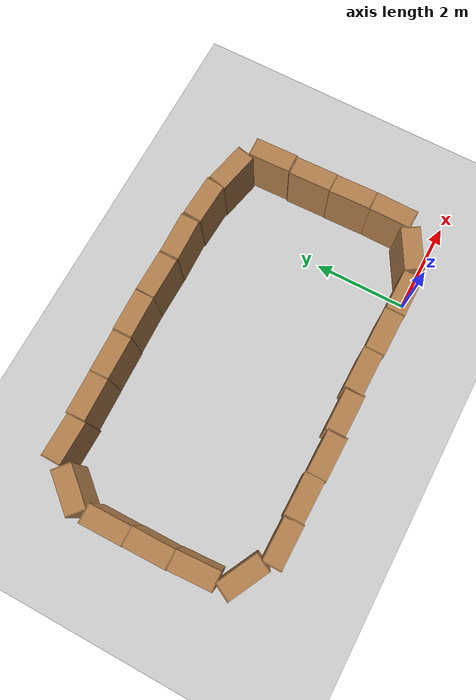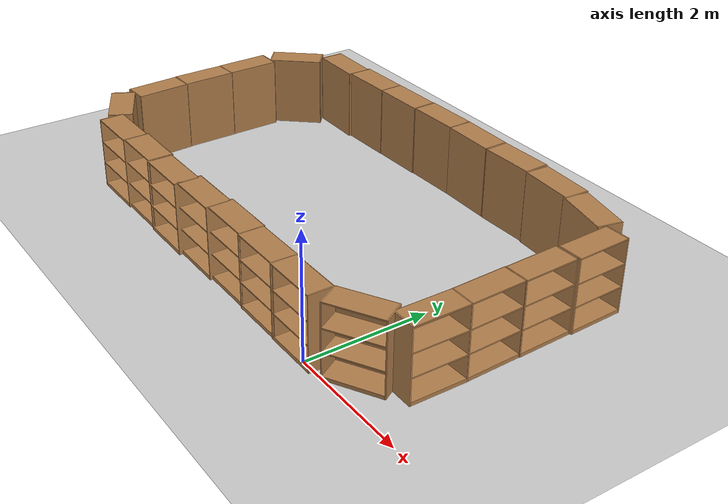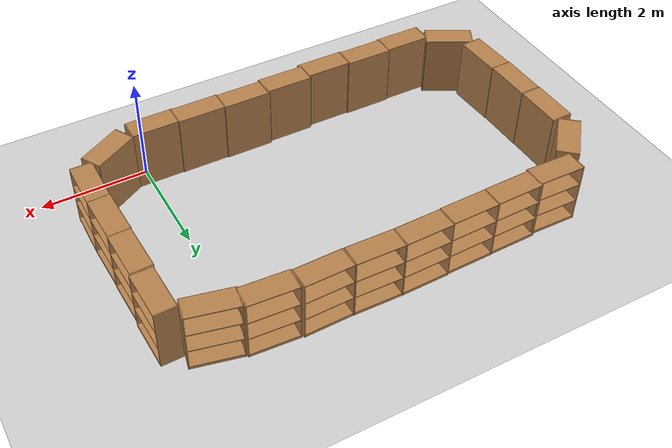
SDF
<sdf version="1.4">
 <world name="default">
  <light name="sun" type="directional">
   <pose>0 0 10 0 -0 0</pose>
   <diffuse>0.8 0.8 0.8 1</diffuse>
   <specular>0.2 0.2 0.2 1</specular>
   <attenuation>
    <range>1000</range>
    <constant>0.9</constant>
    <linear>0.01</linear>
    <quadratic>0.001</quadratic>
   </attenuation>
   <direction>-0.5 0.1 -0.9</direction>
  </light>
  <model name="ground_plane">
   <static>1</static>
   <link name="link">
    <collision name="collision">
     <geometry><plane><normal>0 0 1</normal><size>100 100</size></plane></geometry>
     <surface><friction><ode><mu>100</mu><mu2>50</mu2></ode></friction></surface>
    </collision>
    <visual name="visual">
     <cast_shadows>0</cast_shadows>
     <geometry><plane><normal>0 0 1</normal><size>100 100</size></plane></geometry>
     <material>
      <script><uri>file://media/materials/scripts/gazebo.material</uri><name>Gazebo/Grey</name></script>
     </material>
    </visual>
    <velocity_decay><linear>0</linear><angular>0</angular></velocity_decay>
   </link>
  </model>
  <physics type="ode">
   <max_step_size>0.01</max_step_size>
   <real_time_factor>1</real_time_factor>
   <real_time_update_rate>100</real_time_update_rate>
   <gravity>0 0 -9.8</gravity>
  </physics>
  <scene><ambient>0.4 0.4 0.4 1</ambient><background>0.7 0.7 0.7 1</background><shadows>1</shadows></scene>
  <model name="bookshelf">
   <static>1</static>
   <link name="link">
    <inertial><mass>1</mass></inertial>
    <collision name="back">
     <pose>0 0.005 0.6 0 -0 0</pose>
     <geometry><box><size>0.9 0.01 1.2</size></box></geometry>
    </collision>
    <visual name="visual1">
     <pose>0 0.005 0.6 0 -0 0</pose>
     <geometry><box><size>0.9 0.01 1.2</size></box></geometry>
     <material>
      <script><uri>file://media/materials/scripts/gazebo.material</uri><name>Gazebo/Wood</name></script>
     </material>
    </visual>
    <collision name="left_side">
     <pose>0.45 -0.195 0.6 0 -0 0</pose>
     <geometry><box><size>0.02 0.4 1.2</size></box></geometry>
    </collision>
    <visual name="visual2">
     <pose>0.45 -0.195 0.6 0 -0 0</pose>
     <geometry><box><size>0.02 0.4 1.2</size></box></geometry>
     <material>
      <script><uri>file://media/materials/scripts/gazebo.material</uri><name>Gazebo/Wood</name></script>
     </material>
    </visual>
    <collision name="right_side">
     <pose>-0.45 -0.195 0.6 0 -0 0</pose>
     <geometry><box><size>0.02 0.4 1.2</size></box></geometry>
    </collision>
    <visual name="visual3">
     <pose>-0.45 -0.195 0.6 0 -0 0</pose>
     <geometry><box><size>0.02 0.4 1.2</size></box></geometry>
     <material>
      <script><uri>file://media/materials/scripts/gazebo.material</uri><name>Gazebo/Wood</name></script>
     </material>
    </visual>
    <collision name="bottom">
     <pose>0 -0.195 0.03 0 -0 0</pose>
     <geometry><box><size>0.88 0.4 0.06</size></box></geometry>
    </collision>
    <visual name="visual4">
     <pose>0 -0.195 0.03 0 -0 0</pose>
     <geometry><box><size>0.88 0.4 0.06</size></box></geometry>
     <material>
      <script><uri>file://media/materials/scripts/gazebo.material</uri><name>Gazebo/Wood</name></script>
     </material>
    </visual>
    <collision name="top">
     <pose>0 -0.195 1.19 0 -0 0</pose>
     <geometry><box><size>0.88 0.4 0.02</size></box></geometry>
    </collision>
    <visual name="visual5">
     <pose>0 -0.195 1.19 0 -0 0</pose>
     <geometry><box><size>0.88 0.4 0.02</size></box></geometry>
     <material>
      <script><uri>file://media/materials/scripts/gazebo.material</uri><name>Gazebo/Wood</name></script>
     </material>
    </visual>
    <collision name="low_shelf">
     <pose>0 -0.195 0.43 0 -0 0</pose>
     <geometry><box><size>0.88 0.4 0.02</size></box></geometry>
    </collision>
    <visual name="visual6">
     <pose>0 -0.195 0.43 0 -0 0</pose>
     <geometry><box><size>0.88 0.4 0.02</size></box></geometry>
     <material>
      <script><uri>file://media/materials/scripts/gazebo.material</uri><name>Gazebo/Wood</name></script>
     </material>
    </visual>
    <collision name="high_shelf">
     <pose>0 -0.195 0.8 0 -0 0</pose>
     <geometry><box><size>0.88 0.4 0.02</size></box></geometry>
    </collision>
    <visual name="visual7">
     <pose>0 -0.195 0.8 0 -0 0</pose>
     <geometry><box><size>0.88 0.4 0.02</size></box></geometry>
     <material>
      <script><uri>file://media/materials/scripts/gazebo.material</uri><name>Gazebo/Wood</name></script>
     </material>
    </visual>
    <velocity_decay><linear>0</linear><angular>0</angular></velocity_decay>
   </link>
   <pose>-2.84726 0.305303 0 0 -0 0</pose>
  </model>
  <model name="bookshelf_0">
   <static>1</static>
   <link name="link">
    <inertial><mass>1</mass></inertial>
    <collision name="back">
     <pose>0 0.005 0.6 0 -0 0</pose>
     <geometry><box><size>0.9 0.01 1.2</size></box></geometry>
    </collision>
    <visual name="visual1">
     <pose>0 0.005 0.6 0 -0 0</pose>
     <geometry><box><size>0.9 0.01 1.2</size></box></geometry>
     <material>
      <script><uri>file://media/materials/scripts/gazebo.material</uri><name>Gazebo/Wood</name></script>
     </material>
    </visual>
    <collision name="left_side">
     <pose>0.45 -0.195 0.6 0 -0 0</pose>
     <geometry><box><size>0.02 0.4 1.2</size></box></geometry>
    </collision>
    <visual name="visual2">
     <pose>0.45 -0.195 0.6 0 -0 0</pose>
     <geometry><box><size>0.02 0.4 1.2</size></box></geometry>
     <material>
      <script><uri>file://media/materials/scripts/gazebo.material</uri><name>Gazebo/Wood</name></script>
     </material>
    </visual>
    <collision name="right_side">
     <pose>-0.45 -0.195 0.6 0 -0 0</pose>
     <geometry><box><size>0.02 0.4 1.2</size></box></geometry>
    </collision>
    <visual name="visual3">
     <pose>-0.45 -0.195 0.6 0 -0 0</pose>
     <geometry><box><size>0.02 0.4 1.2</size></box></geometry>
     <material>
      <script><uri>file://media/materials/scripts/gazebo.material</uri><name>Gazebo/Wood</name></script>
     </material>
    </visual>
    <collision name="bottom">
     <pose>0 -0.195 0.03 0 -0 0</pose>
     <geometry><box><size>0.88 0.4 0.06</size></box></geometry>
    </collision>
    <visual name="visual4">
     <pose>0 -0.195 0.03 0 -0 0</pose>
     <geometry><box><size>0.88 0.4 0.06</size></box></geometry>
     <material>
      <script><uri>file://media/materials/scripts/gazebo.material</uri><name>Gazebo/Wood</name></script>
     </material>
    </visual>
    <collision name="top">
     <pose>0 -0.195 1.19 0 -0 0</pose>
     <geometry><box><size>0.88 0.4 0.02</size></box></geometry>
    </collision>
    <visual name="visual5">
     <pose>0 -0.195 1.19 0 -0 0</pose>
     <geometry><box><size>0.88 0.4 0.02</size></box></geometry>
     <material>
      <script><uri>file://media/materials/scripts/gazebo.material</uri><name>Gazebo/Wood</name></script>
     </material>
    </visual>
    <collision name="low_shelf">
     <pose>0 -0.195 0.43 0 -0 0</pose>
     <geometry><box><size>0.88 0.4 0.02</size></box></geometry>
    </collision>
    <visual name="visual6">
     <pose>0 -0.195 0.43 0 -0 0</pose>
     <geometry><box><size>0.88 0.4 0.02</size></box></geometry>
     <material>
      <script><uri>file://media/materials/scripts/gazebo.material</uri><name>Gazebo/Wood</name></script>
     </material>
    </visual>
    <collision name="high_shelf">
     <pose>0 -0.195 0.8 0 -0 0</pose>
     <geometry><box><size>0.88 0.4 0.02</size></box></geometry>
    </collision>
    <visual name="visual7">
     <pose>0 -0.195 0.8 0 -0 0</pose>
     <geometry><box><size>0.88 0.4 0.02</size></box></geometry>
     <material>
      <script><uri>file://media/materials/scripts/gazebo.material</uri><name>Gazebo/Wood</name></script>
     </material>
    </visual>
    <velocity_decay><linear>0</linear><angular>0</angular></velocity_decay>
   </link>
   <pose>-1.96662 0.347335 0 0 -0 0</pose>
  </model>
  <model name="bookshelf_1">
   <static>1</static>
   <link name="link">
    <inertial><mass>1</mass></inertial>
    <collision name="back">
     <pose>0 0.005 0.6 0 -0 0</pose>
     <geometry><box><size>0.9 0.01 1.2</size></box></geometry>
    </collision>
    <visual name="visual1">
     <pose>0 0.005 0.6 0 -0 0</pose>
     <geometry><box><size>0.9 0.01 1.2</size></box></geometry>
     <material>
      <script><uri>file://media/materials/scripts/gazebo.material</uri><name>Gazebo/Wood</name></script>
     </material>
    </visual>
    <collision name="left_side">
     <pose>0.45 -0.195 0.6 0 -0 0</pose>
     <geometry><box><size>0.02 0.4 1.2</size></box></geometry>
    </collision>
    <visual name="visual2">
     <pose>0.45 -0.195 0.6 0 -0 0</pose>
     <geometry><box><size>0.02 0.4 1.2</size></box></geometry>
     <material>
      <script><uri>file://media/materials/scripts/gazebo.material</uri><name>Gazebo/Wood</name></script>
     </material>
    </visual>
    <collision name="right_side">
     <pose>-0.45 -0.195 0.6 0 -0 0</pose>
     <geometry><box><size>0.02 0.4 1.2</size></box></geometry>
    </collision>
    <visual name="visual3">
     <pose>-0.45 -0.195 0.6 0 -0 0</pose>
     <geometry><box><size>0.02 0.4 1.2</size></box></geometry>
     <material>
      <script><uri>file://media/materials/scripts/gazebo.material</uri><name>Gazebo/Wood</name></script>
     </material>
    </visual>
    <collision name="bottom">
     <pose>0 -0.195 0.03 0 -0 0</pose>
     <geometry><box><size>0.88 0.4 0.06</size></box></geometry>
    </collision>
    <visual name="visual4">
     <pose>0 -0.195 0.03 0 -0 0</pose>
     <geometry><box><size>0.88 0.4 0.06</size></box></geometry>
     <material>
      <script><uri>file://media/materials/scripts/gazebo.material</uri><name>Gazebo/Wood</name></script>
     </material>
    </visual>
    <collision name="top">
     <pose>0 -0.195 1.19 0 -0 0</pose>
     <geometry><box><size>0.88 0.4 0.02</size></box></geometry>
    </collision>
    <visual name="visual5">
     <pose>0 -0.195 1.19 0 -0 0</pose>
     <geometry><box><size>0.88 0.4 0.02</size></box></geometry>
     <material>
      <script><uri>file://media/materials/scripts/gazebo.material</uri><name>Gazebo/Wood</name></script>
     </material>
    </visual>
    <collision name="low_shelf">
     <pose>0 -0.195 0.43 0 -0 0</pose>
     <geometry><box><size>0.88 0.4 0.02</size></box></geometry>
    </collision>
    <visual name="visual6">
     <pose>0 -0.195 0.43 0 -0 0</pose>
     <geometry><box><size>0.88 0.4 0.02</size></box></geometry>
     <material>
      <script><uri>file://media/materials/scripts/gazebo.material</uri><name>Gazebo/Wood</name></script>
     </material>
    </visual>
    <collision name="high_shelf">
     <pose>0 -0.195 0.8 0 -0 0</pose>
     <geometry><box><size>0.88 0.4 0.02</size></box></geometry>
    </collision>
    <visual name="visual7">
     <pose>0 -0.195 0.8 0 -0 0</pose>
     <geometry><box><size>0.88 0.4 0.02</size></box></geometry>
     <material>
      <script><uri>file://media/materials/scripts/gazebo.material</uri><name>Gazebo/Wood</name></script>
     </material>
    </visual>
    <velocity_decay><linear>0</linear><angular>0</angular></velocity_decay>
   </link>
   <pose>-1.07116 0.328228 0 0 -0 0</pose>
  </model>
  <model name="bookshelf_2">
   <static>1</static>
   <link name="link">
    <inertial><mass>1</mass></inertial>
    <collision name="back">
     <pose>0 0.005 0.6 0 -0 0</pose>
     <geometry><box><size>0.9 0.01 1.2</size></box></geometry>
    </collision>
    <visual name="visual1">
     <pose>0 0.005 0.6 0 -0 0</pose>
     <geometry><box><size>0.9 0.01 1.2</size></box></geometry>
     <material>
      <script><uri>file://media/materials/scripts/gazebo.material</uri><name>Gazebo/Wood</name></script>
     </material>
    </visual>
    <collision name="left_side">
     <pose>0.45 -0.195 0.6 0 -0 0</pose>
     <geometry><box><size>0.02 0.4 1.2</size></box></geometry>
    </collision>
    <visual name="visual2">
     <pose>0.45 -0.195 0.6 0 -0 0</pose>
     <geometry><box><size>0.02 0.4 1.2</size></box></geometry>
     <material>
      <script><uri>file://media/materials/scripts/gazebo.material</uri><name>Gazebo/Wood</name></script>
     </material>
    </visual>
    <collision name="right_side">
     <pose>-0.45 -0.195 0.6 0 -0 0</pose>
     <geometry><box><size>0.02 0.4 1.2</size></box></geometry>
    </collision>
    <visual name="visual3">
     <pose>-0.45 -0.195 0.6 0 -0 0</pose>
     <geometry><box><size>0.02 0.4 1.2</size></box></geometry>
     <material>
      <script><uri>file://media/materials/scripts/gazebo.material</uri><name>Gazebo/Wood</name></script>
     </material>
    </visual>
    <collision name="bottom">
     <pose>0 -0.195 0.03 0 -0 0</pose>
     <geometry><box><size>0.88 0.4 0.06</size></box></geometry>
    </collision>
    <visual name="visual4">
     <pose>0 -0.195 0.03 0 -0 0</pose>
     <geometry><box><size>0.88 0.4 0.06</size></box></geometry>
     <material>
      <script><uri>file://media/materials/scripts/gazebo.material</uri><name>Gazebo/Wood</name></script>
     </material>
    </visual>
    <collision name="top">
     <pose>0 -0.195 1.19 0 -0 0</pose>
     <geometry><box><size>0.88 0.4 0.02</size></box></geometry>
    </collision>
    <visual name="visual5">
     <pose>0 -0.195 1.19 0 -0 0</pose>
     <geometry><box><size>0.88 0.4 0.02</size></box></geometry>
     <material>
      <script><uri>file://media/materials/scripts/gazebo.material</uri><name>Gazebo/Wood</name></script>
     </material>
    </visual>
    <collision name="low_shelf">
     <pose>0 -0.195 0.43 0 -0 0</pose>
     <geometry><box><size>0.88 0.4 0.02</size></box></geometry>
    </collision>
    <visual name="visual6">
     <pose>0 -0.195 0.43 0 -0 0</pose>
     <geometry><box><size>0.88 0.4 0.02</size></box></geometry>
     <material>
      <script><uri>file://media/materials/scripts/gazebo.material</uri><name>Gazebo/Wood</name></script>
     </material>
    </visual>
    <collision name="high_shelf">
     <pose>0 -0.195 0.8 0 -0 0</pose>
     <geometry><box><size>0.88 0.4 0.02</size></box></geometry>
    </collision>
    <visual name="visual7">
     <pose>0 -0.195 0.8 0 -0 0</pose>
     <geometry><box><size>0.88 0.4 0.02</size></box></geometry>
     <material>
      <script><uri>file://media/materials/scripts/gazebo.material</uri><name>Gazebo/Wood</name></script>
     </material>
    </visual>
    <velocity_decay><linear>0</linear><angular>0</angular></velocity_decay>
   </link>
   <pose>-0.202462 0.315464 0 0 -0 0</pose>
  </model>
  <model name="bookshelf_3">
   <static>1</static>
   <link name="link">
    <inertial><mass>1</mass></inertial>
    <collision name="back">
     <pose>0 0.005 0.6 0 -0 0</pose>
     <geometry><box><size>0.9 0.01 1.2</size></box></geometry>
    </collision>
    <visual name="visual1">
     <pose>0 0.005 0.6 0 -0 0</pose>
     <geometry><box><size>0.9 0.01 1.2</size></box></geometry>
     <material>
      <script><uri>file://media/materials/scripts/gazebo.material</uri><name>Gazebo/Wood</name></script>
     </material>
    </visual>
    <collision name="left_side">
     <pose>0.45 -0.195 0.6 0 -0 0</pose>
     <geometry><box><size>0.02 0.4 1.2</size></box></geometry>
    </collision>
    <visual name="visual2">
     <pose>0.45 -0.195 0.6 0 -0 0</pose>
     <geometry><box><size>0.02 0.4 1.2</size></box></geometry>
     <material>
      <script><uri>file://media/materials/scripts/gazebo.material</uri><name>Gazebo/Wood</name></script>
     </material>
    </visual>
    <collision name="right_side">
     <pose>-0.45 -0.195 0.6 0 -0 0</pose>
     <geometry><box><size>0.02 0.4 1.2</size></box></geometry>
    </collision>
    <visual name="visual3">
     <pose>-0.45 -0.195 0.6 0 -0 0</pose>
     <geometry><box><size>0.02 0.4 1.2</size></box></geometry>
     <material>
      <script><uri>file://media/materials/scripts/gazebo.material</uri><name>Gazebo/Wood</name></script>
     </material>
    </visual>
    <collision name="bottom">
     <pose>0 -0.195 0.03 0 -0 0</pose>
     <geometry><box><size>0.88 0.4 0.06</size></box></geometry>
    </collision>
    <visual name="visual4">
     <pose>0 -0.195 0.03 0 -0 0</pose>
     <geometry><box><size>0.88 0.4 0.06</size></box></geometry>
     <material>
      <script><uri>file://media/materials/scripts/gazebo.material</uri><name>Gazebo/Wood</name></script>
     </material>
    </visual>
    <collision name="top">
     <pose>0 -0.195 1.19 0 -0 0</pose>
     <geometry><box><size>0.88 0.4 0.02</size></box></geometry>
    </collision>
    <visual name="visual5">
     <pose>0 -0.195 1.19 0 -0 0</pose>
     <geometry><box><size>0.88 0.4 0.02</size></box></geometry>
     <material>
      <script><uri>file://media/materials/scripts/gazebo.material</uri><name>Gazebo/Wood</name></script>
     </material>
    </visual>
    <collision name="low_shelf">
     <pose>0 -0.195 0.43 0 -0 0</pose>
     <geometry><box><size>0.88 0.4 0.02</size></box></geometry>
    </collision>
    <visual name="visual6">
     <pose>0 -0.195 0.43 0 -0 0</pose>
     <geometry><box><size>0.88 0.4 0.02</size></box></geometry>
     <material>
      <script><uri>file://media/materials/scripts/gazebo.material</uri><name>Gazebo/Wood</name></script>
     </material>
    </visual>
    <collision name="high_shelf">
     <pose>0 -0.195 0.8 0 -0 0</pose>
     <geometry><box><size>0.88 0.4 0.02</size></box></geometry>
    </collision>
    <visual name="visual7">
     <pose>0 -0.195 0.8 0 -0 0</pose>
     <geometry><box><size>0.88 0.4 0.02</size></box></geometry>
     <material>
      <script><uri>file://media/materials/scripts/gazebo.material</uri><name>Gazebo/Wood</name></script>
     </material>
    </visual>
    <velocity_decay><linear>0</linear><angular>0</angular></velocity_decay>
   </link>
   <pose>0.640669 0.550487 0 0 -0 0.52</pose>
  </model>
  <model name="bookshelf_4">
   <static>1</static>
   <link name="link">
    <inertial><mass>1</mass></inertial>
    <collision name="back">
     <pose>0 0.005 0.6 0 -0 0</pose>
     <geometry><box><size>0.9 0.01 1.2</size></box></geometry>
    </collision>
    <visual name="visual1">
     <pose>0 0.005 0.6 0 -0 0</pose>
     <geometry><box><size>0.9 0.01 1.2</size></box></geometry>
     <material>
      <script><uri>file://media/materials/scripts/gazebo.material</uri><name>Gazebo/Wood</name></script>
     </material>
    </visual>
    <collision name="left_side">
     <pose>0.45 -0.195 0.6 0 -0 0</pose>
     <geometry><box><size>0.02 0.4 1.2</size></box></geometry>
    </collision>
    <visual name="visual2">
     <pose>0.45 -0.195 0.6 0 -0 0</pose>
     <geometry><box><size>0.02 0.4 1.2</size></box></geometry>
     <material>
      <script><uri>file://media/materials/scripts/gazebo.material</uri><name>Gazebo/Wood</name></script>
     </material>
    </visual>
    <collision name="right_side">
     <pose>-0.45 -0.195 0.6 0 -0 0</pose>
     <geometry><box><size>0.02 0.4 1.2</size></box></geometry>
    </collision>
    <visual name="visual3">
     <pose>-0.45 -0.195 0.6 0 -0 0</pose>
     <geometry><box><size>0.02 0.4 1.2</size></box></geometry>
     <material>
      <script><uri>file://media/materials/scripts/gazebo.material</uri><name>Gazebo/Wood</name></script>
     </material>
    </visual>
    <collision name="bottom">
     <pose>0 -0.195 0.03 0 -0 0</pose>
     <geometry><box><size>0.88 0.4 0.06</size></box></geometry>
    </collision>
    <visual name="visual4">
     <pose>0 -0.195 0.03 0 -0 0</pose>
     <geometry><box><size>0.88 0.4 0.06</size></box></geometry>
     <material>
      <script><uri>file://media/materials/scripts/gazebo.material</uri><name>Gazebo/Wood</name></script>
     </material>
    </visual>
    <collision name="top">
     <pose>0 -0.195 1.19 0 -0 0</pose>
     <geometry><box><size>0.88 0.4 0.02</size></box></geometry>
    </collision>
    <visual name="visual5">
     <pose>0 -0.195 1.19 0 -0 0</pose>
     <geometry><box><size>0.88 0.4 0.02</size></box></geometry>
     <material>
      <script><uri>file://media/materials/scripts/gazebo.material</uri><name>Gazebo/Wood</name></script>
     </material>
    </visual>
    <collision name="low_shelf">
     <pose>0 -0.195 0.43 0 -0 0</pose>
     <geometry><box><size>0.88 0.4 0.02</size></box></geometry>
    </collision>
    <visual name="visual6">
     <pose>0 -0.195 0.43 0 -0 0</pose>
     <geometry><box><size>0.88 0.4 0.02</size></box></geometry>
     <material>
      <script><uri>file://media/materials/scripts/gazebo.material</uri><name>Gazebo/Wood</name></script>
     </material>
    </visual>
    <collision name="high_shelf">
     <pose>0 -0.195 0.8 0 -0 0</pose>
     <geometry><box><size>0.88 0.4 0.02</size></box></geometry>
    </collision>
    <visual name="visual7">
     <pose>0 -0.195 0.8 0 -0 0</pose>
     <geometry><box><size>0.88 0.4 0.02</size></box></geometry>
     <material>
      <script><uri>file://media/materials/scripts/gazebo.material</uri><name>Gazebo/Wood</name></script>
     </material>
    </visual>
    <velocity_decay><linear>0</linear><angular>0</angular></velocity_decay>
   </link>
   <pose>-3.91852 4.37082 0 0 0 -3.12</pose>
  </model>
  <model name="bookshelf_5">
   <static>1</static>
   <link name="link">
    <inertial><mass>1</mass></inertial>
    <collision name="back">
     <pose>0 0.005 0.6 0 -0 0</pose>
     <geometry><box><size>0.9 0.01 1.2</size></box></geometry>
    </collision>
    <visual name="visual1">
     <pose>0 0.005 0.6 0 -0 0</pose>
     <geometry><box><size>0.9 0.01 1.2</size></box></geometry>
     <material>
      <script><uri>file://media/materials/scripts/gazebo.material</uri><name>Gazebo/Wood</name></script>
     </material>
    </visual>
    <collision name="left_side">
     <pose>0.45 -0.195 0.6 0 -0 0</pose>
     <geometry><box><size>0.02 0.4 1.2</size></box></geometry>
    </collision>
    <visual name="visual2">
     <pose>0.45 -0.195 0.6 0 -0 0</pose>
     <geometry><box><size>0.02 0.4 1.2</size></box></geometry>
     <material>
      <script><uri>file://media/materials/scripts/gazebo.material</uri><name>Gazebo/Wood</name></script>
     </material>
    </visual>
    <collision name="right_side">
     <pose>-0.45 -0.195 0.6 0 -0 0</pose>
     <geometry><box><size>0.02 0.4 1.2</size></box></geometry>
    </collision>
    <visual name="visual3">
     <pose>-0.45 -0.195 0.6 0 -0 0</pose>
     <geometry><box><size>0.02 0.4 1.2</size></box></geometry>
     <material>
      <script><uri>file://media/materials/scripts/gazebo.material</uri><name>Gazebo/Wood</name></script>
     </material>
    </visual>
    <collision name="bottom">
     <pose>0 -0.195 0.03 0 -0 0</pose>
     <geometry><box><size>0.88 0.4 0.06</size></box></geometry>
    </collision>
    <visual name="visual4">
     <pose>0 -0.195 0.03 0 -0 0</pose>
     <geometry><box><size>0.88 0.4 0.06</size></box></geometry>
     <material>
      <script><uri>file://media/materials/scripts/gazebo.material</uri><name>Gazebo/Wood</name></script>
     </material>
    </visual>
    <collision name="top">
     <pose>0 -0.195 1.19 0 -0 0</pose>
     <geometry><box><size>0.88 0.4 0.02</size></box></geometry>
    </collision>
    <visual name="visual5">
     <pose>0 -0.195 1.19 0 -0 0</pose>
     <geometry><box><size>0.88 0.4 0.02</size></box></geometry>
     <material>
      <script><uri>file://media/materials/scripts/gazebo.material</uri><name>Gazebo/Wood</name></script>
     </material>
    </visual>
    <collision name="low_shelf">
     <pose>0 -0.195 0.43 0 -0 0</pose>
     <geometry><box><size>0.88 0.4 0.02</size></box></geometry>
    </collision>
    <visual name="visual6">
     <pose>0 -0.195 0.43 0 -0 0</pose>
     <geometry><box><size>0.88 0.4 0.02</size></box></geometry>
     <material>
      <script><uri>file://media/materials/scripts/gazebo.material</uri><name>Gazebo/Wood</name></script>
     </material>
    </visual>
    <collision name="high_shelf">
     <pose>0 -0.195 0.8 0 -0 0</pose>
     <geometry><box><size>0.88 0.4 0.02</size></box></geometry>
    </collision>
    <visual name="visual7">
     <pose>0 -0.195 0.8 0 -0 0</pose>
     <geometry><box><size>0.88 0.4 0.02</size></box></geometry>
     <material>
      <script><uri>file://media/materials/scripts/gazebo.material</uri><name>Gazebo/Wood</name></script>
     </material>
    </visual>
    <velocity_decay><linear>0</linear><angular>0</angular></velocity_decay>
   </link>
   <pose>-3.00921 4.40269 0 0 0 -3.12</pose>
  </model>
  <model name="bookshelf_6">
   <static>1</static>
   <link name="link">
    <inertial><mass>1</mass></inertial>
    <collision name="back">
     <pose>0 0.005 0.6 0 -0 0</pose>
     <geometry><box><size>0.9 0.01 1.2</size></box></geometry>
    </collision>
    <visual name="visual1">
     <pose>0 0.005 0.6 0 -0 0</pose>
     <geometry><box><size>0.9 0.01 1.2</size></box></geometry>
     <material>
      <script><uri>file://media/materials/scripts/gazebo.material</uri><name>Gazebo/Wood</name></script>
     </material>
    </visual>
    <collision name="left_side">
     <pose>0.45 -0.195 0.6 0 -0 0</pose>
     <geometry><box><size>0.02 0.4 1.2</size></box></geometry>
    </collision>
    <visual name="visual2">
     <pose>0.45 -0.195 0.6 0 -0 0</pose>
     <geometry><box><size>0.02 0.4 1.2</size></box></geometry>
     <material>
      <script><uri>file://media/materials/scripts/gazebo.material</uri><name>Gazebo/Wood</name></script>
     </material>
    </visual>
    <collision name="right_side">
     <pose>-0.45 -0.195 0.6 0 -0 0</pose>
     <geometry><box><size>0.02 0.4 1.2</size></box></geometry>
    </collision>
    <visual name="visual3">
     <pose>-0.45 -0.195 0.6 0 -0 0</pose>
     <geometry><box><size>0.02 0.4 1.2</size></box></geometry>
     <material>
      <script><uri>file://media/materials/scripts/gazebo.material</uri><name>Gazebo/Wood</name></script>
     </material>
    </visual>
    <collision name="bottom">
     <pose>0 -0.195 0.03 0 -0 0</pose>
     <geometry><box><size>0.88 0.4 0.06</size></box></geometry>
    </collision>
    <visual name="visual4">
     <pose>0 -0.195 0.03 0 -0 0</pose>
     <geometry><box><size>0.88 0.4 0.06</size></box></geometry>
     <material>
      <script><uri>file://media/materials/scripts/gazebo.material</uri><name>Gazebo/Wood</name></script>
     </material>
    </visual>
    <collision name="top">
     <pose>0 -0.195 1.19 0 -0 0</pose>
     <geometry><box><size>0.88 0.4 0.02</size></box></geometry>
    </collision>
    <visual name="visual5">
     <pose>0 -0.195 1.19 0 -0 0</pose>
     <geometry><box><size>0.88 0.4 0.02</size></box></geometry>
     <material>
      <script><uri>file://media/materials/scripts/gazebo.material</uri><name>Gazebo/Wood</name></script>
     </material>
    </visual>
    <collision name="low_shelf">
     <pose>0 -0.195 0.43 0 -0 0</pose>
     <geometry><box><size>0.88 0.4 0.02</size></box></geometry>
    </collision>
    <visual name="visual6">
     <pose>0 -0.195 0.43 0 -0 0</pose>
     <geometry><box><size>0.88 0.4 0.02</size></box></geometry>
     <material>
      <script><uri>file://media/materials/scripts/gazebo.material</uri><name>Gazebo/Wood</name></script>
     </material>
    </visual>
    <collision name="high_shelf">
     <pose>0 -0.195 0.8 0 -0 0</pose>
     <geometry><box><size>0.88 0.4 0.02</size></box></geometry>
    </collision>
    <visual name="visual7">
     <pose>0 -0.195 0.8 0 -0 0</pose>
     <geometry><box><size>0.88 0.4 0.02</size></box></geometry>
     <material>
      <script><uri>file://media/materials/scripts/gazebo.material</uri><name>Gazebo/Wood</name></script>
     </material>
    </visual>
    <velocity_decay><linear>0</linear><angular>0</angular></velocity_decay>
   </link>
   <pose>-2.11756 4.40334 0 0 -0 3.12318</pose>
  </model>
  <model name="bookshelf_7">
   <static>1</static>
   <link name="link">
    <inertial><mass>1</mass></inertial>
    <collision name="back">
     <pose>0 0.005 0.6 0 -0 0</pose>
     <geometry><box><size>0.9 0.01 1.2</size></box></geometry>
    </collision>
    <visual name="visual1">
     <pose>0 0.005 0.6 0 -0 0</pose>
     <geometry><box><size>0.9 0.01 1.2</size></box></geometry>
     <material>
      <script><uri>file://media/materials/scripts/gazebo.material</uri><name>Gazebo/Wood</name></script>
     </material>
    </visual>
    <collision name="left_side">
     <pose>0.45 -0.195 0.6 0 -0 0</pose>
     <geometry><box><size>0.02 0.4 1.2</size></box></geometry>
    </collision>
    <visual name="visual2">
     <pose>0.45 -0.195 0.6 0 -0 0</pose>
     <geometry><box><size>0.02 0.4 1.2</size></box></geometry>
     <material>
      <script><uri>file://media/materials/scripts/gazebo.material</uri><name>Gazebo/Wood</name></script>
     </material>
    </visual>
    <collision name="right_side">
     <pose>-0.45 -0.195 0.6 0 -0 0</pose>
     <geometry><box><size>0.02 0.4 1.2</size></box></geometry>
    </collision>
    <visual name="visual3">
     <pose>-0.45 -0.195 0.6 0 -0 0</pose>
     <geometry><box><size>0.02 0.4 1.2</size></box></geometry>
     <material>
      <script><uri>file://media/materials/scripts/gazebo.material</uri><name>Gazebo/Wood</name></script>
     </material>
    </visual>
    <collision name="bottom">
     <pose>0 -0.195 0.03 0 -0 0</pose>
     <geometry><box><size>0.88 0.4 0.06</size></box></geometry>
    </collision>
    <visual name="visual4">
     <pose>0 -0.195 0.03 0 -0 0</pose>
     <geometry><box><size>0.88 0.4 0.06</size></box></geometry>
     <material>
      <script><uri>file://media/materials/scripts/gazebo.material</uri><name>Gazebo/Wood</name></script>
     </material>
    </visual>
    <collision name="top">
     <pose>0 -0.195 1.19 0 -0 0</pose>
     <geometry><box><size>0.88 0.4 0.02</size></box></geometry>
    </collision>
    <visual name="visual5">
     <pose>0 -0.195 1.19 0 -0 0</pose>
     <geometry><box><size>0.88 0.4 0.02</size></box></geometry>
     <material>
      <script><uri>file://media/materials/scripts/gazebo.material</uri><name>Gazebo/Wood</name></script>
     </material>
    </visual>
    <collision name="low_shelf">
     <pose>0 -0.195 0.43 0 -0 0</pose>
     <geometry><box><size>0.88 0.4 0.02</size></box></geometry>
    </collision>
    <visual name="visual6">
     <pose>0 -0.195 0.43 0 -0 0</pose>
     <geometry><box><size>0.88 0.4 0.02</size></box></geometry>
     <material>
      <script><uri>file://media/materials/scripts/gazebo.material</uri><name>Gazebo/Wood</name></script>
     </material>
    </visual>
    <collision name="high_shelf">
     <pose>0 -0.195 0.8 0 -0 0</pose>
     <geometry><box><size>0.88 0.4 0.02</size></box></geometry>
    </collision>
    <visual name="visual7">
     <pose>0 -0.195 0.8 0 -0 0</pose>
     <geometry><box><size>0.88 0.4 0.02</size></box></geometry>
     <material>
      <script><uri>file://media/materials/scripts/gazebo.material</uri><name>Gazebo/Wood</name></script>
     </material>
    </visual>
    <velocity_decay><linear>0</linear><angular>0</angular></velocity_decay>
   </link>
   <pose>-1.19087 4.40083 0 0 0 -3.12</pose>
  </model>
  <model name="bookshelf_8">
   <static>1</static>
   <link name="link">
    <inertial><mass>1</mass></inertial>
    <collision name="back">
     <pose>0 0.005 0.6 0 -0 0</pose>
     <geometry><box><size>0.9 0.01 1.2</size></box></geometry>
    </collision>
    <visual name="visual1">
     <pose>0 0.005 0.6 0 -0 0</pose>
     <geometry><box><size>0.9 0.01 1.2</size></box></geometry>
     <material>
      <script><uri>file://media/materials/scripts/gazebo.material</uri><name>Gazebo/Wood</name></script>
     </material>
    </visual>
    <collision name="left_side">
     <pose>0.45 -0.195 0.6 0 -0 0</pose>
     <geometry><box><size>0.02 0.4 1.2</size></box></geometry>
    </collision>
    <visual name="visual2">
     <pose>0.45 -0.195 0.6 0 -0 0</pose>
     <geometry><box><size>0.02 0.4 1.2</size></box></geometry>
     <material>
      <script><uri>file://media/materials/scripts/gazebo.material</uri><name>Gazebo/Wood</name></script>
     </material>
    </visual>
    <collision name="right_side">
     <pose>-0.45 -0.195 0.6 0 -0 0</pose>
     <geometry><box><size>0.02 0.4 1.2</size></box></geometry>
    </collision>
    <visual name="visual3">
     <pose>-0.45 -0.195 0.6 0 -0 0</pose>
     <geometry><box><size>0.02 0.4 1.2</size></box></geometry>
     <material>
      <script><uri>file://media/materials/scripts/gazebo.material</uri><name>Gazebo/Wood</name></script>
     </material>
    </visual>
    <collision name="bottom">
     <pose>0 -0.195 0.03 0 -0 0</pose>
     <geometry><box><size>0.88 0.4 0.06</size></box></geometry>
    </collision>
    <visual name="visual4">
     <pose>0 -0.195 0.03 0 -0 0</pose>
     <geometry><box><size>0.88 0.4 0.06</size></box></geometry>
     <material>
      <script><uri>file://media/materials/scripts/gazebo.material</uri><name>Gazebo/Wood</name></script>
     </material>
    </visual>
    <collision name="top">
     <pose>0 -0.195 1.19 0 -0 0</pose>
     <geometry><box><size>0.88 0.4 0.02</size></box></geometry>
    </collision>
    <visual name="visual5">
     <pose>0 -0.195 1.19 0 -0 0</pose>
     <geometry><box><size>0.88 0.4 0.02</size></box></geometry>
     <material>
      <script><uri>file://media/materials/scripts/gazebo.material</uri><name>Gazebo/Wood</name></script>
     </material>
    </visual>
    <collision name="low_shelf">
     <pose>0 -0.195 0.43 0 -0 0</pose>
     <geometry><box><size>0.88 0.4 0.02</size></box></geometry>
    </collision>
    <visual name="visual6">
     <pose>0 -0.195 0.43 0 -0 0</pose>
     <geometry><box><size>0.88 0.4 0.02</size></box></geometry>
     <material>
      <script><uri>file://media/materials/scripts/gazebo.material</uri><name>Gazebo/Wood</name></script>
     </material>
    </visual>
    <collision name="high_shelf">
     <pose>0 -0.195 0.8 0 -0 0</pose>
     <geometry><box><size>0.88 0.4 0.02</size></box></geometry>
    </collision>
    <visual name="visual7">
     <pose>0 -0.195 0.8 0 -0 0</pose>
     <geometry><box><size>0.88 0.4 0.02</size></box></geometry>
     <material>
      <script><uri>file://media/materials/scripts/gazebo.material</uri><name>Gazebo/Wood</name></script>
     </material>
    </visual>
    <velocity_decay><linear>0</linear><angular>0</angular></velocity_decay>
   </link>
   <pose>-0.279273 4.36332 0 0 -0 3.08318</pose>
  </model>
  <model name="bookshelf_9">
   <static>1</static>
   <link name="link">
    <inertial><mass>1</mass></inertial>
    <collision name="back">
     <pose>0 0.005 0.6 0 -0 0</pose>
     <geometry><box><size>0.9 0.01 1.2</size></box></geometry>
    </collision>
    <visual name="visual1">
     <pose>0 0.005 0.6 0 -0 0</pose>
     <geometry><box><size>0.9 0.01 1.2</size></box></geometry>
     <material>
      <script><uri>file://media/materials/scripts/gazebo.material</uri><name>Gazebo/Wood</name></script>
     </material>
    </visual>
    <collision name="left_side">
     <pose>0.45 -0.195 0.6 0 -0 0</pose>
     <geometry><box><size>0.02 0.4 1.2</size></box></geometry>
    </collision>
    <visual name="visual2">
     <pose>0.45 -0.195 0.6 0 -0 0</pose>
     <geometry><box><size>0.02 0.4 1.2</size></box></geometry>
     <material>
      <script><uri>file://media/materials/scripts/gazebo.material</uri><name>Gazebo/Wood</name></script>
     </material>
    </visual>
    <collision name="right_side">
     <pose>-0.45 -0.195 0.6 0 -0 0</pose>
     <geometry><box><size>0.02 0.4 1.2</size></box></geometry>
    </collision>
    <visual name="visual3">
     <pose>-0.45 -0.195 0.6 0 -0 0</pose>
     <geometry><box><size>0.02 0.4 1.2</size></box></geometry>
     <material>
      <script><uri>file://media/materials/scripts/gazebo.material</uri><name>Gazebo/Wood</name></script>
     </material>
    </visual>
    <collision name="bottom">
     <pose>0 -0.195 0.03 0 -0 0</pose>
     <geometry><box><size>0.88 0.4 0.06</size></box></geometry>
    </collision>
    <visual name="visual4">
     <pose>0 -0.195 0.03 0 -0 0</pose>
     <geometry><box><size>0.88 0.4 0.06</size></box></geometry>
     <material>
      <script><uri>file://media/materials/scripts/gazebo.material</uri><name>Gazebo/Wood</name></script>
     </material>
    </visual>
    <collision name="top">
     <pose>0 -0.195 1.19 0 -0 0</pose>
     <geometry><box><size>0.88 0.4 0.02</size></box></geometry>
    </collision>
    <visual name="visual5">
     <pose>0 -0.195 1.19 0 -0 0</pose>
     <geometry><box><size>0.88 0.4 0.02</size></box></geometry>
     <material>
      <script><uri>file://media/materials/scripts/gazebo.material</uri><name>Gazebo/Wood</name></script>
     </material>
    </visual>
    <collision name="low_shelf">
     <pose>0 -0.195 0.43 0 -0 0</pose>
     <geometry><box><size>0.88 0.4 0.02</size></box></geometry>
    </collision>
    <visual name="visual6">
     <pose>0 -0.195 0.43 0 -0 0</pose>
     <geometry><box><size>0.88 0.4 0.02</size></box></geometry>
     <material>
      <script><uri>file://media/materials/scripts/gazebo.material</uri><name>Gazebo/Wood</name></script>
     </material>
    </visual>
    <collision name="high_shelf">
     <pose>0 -0.195 0.8 0 -0 0</pose>
     <geometry><box><size>0.88 0.4 0.02</size></box></geometry>
    </collision>
    <visual name="visual7">
     <pose>0 -0.195 0.8 0 -0 0</pose>
     <geometry><box><size>0.88 0.4 0.02</size></box></geometry>
     <material>
      <script><uri>file://media/materials/scripts/gazebo.material</uri><name>Gazebo/Wood</name></script>
     </material>
    </visual>
    <velocity_decay><linear>0</linear><angular>0</angular></velocity_decay>
   </link>
   <pose>-3.71688 0.248337 0 0 -0 0</pose>
  </model>
  <model name="bookshelf_10">
   <static>1</static>
   <link name="link">
    <inertial><mass>1</mass></inertial>
    <collision name="back">
     <pose>0 0.005 0.6 0 -0 0</pose>
     <geometry><box><size>0.9 0.01 1.2</size></box></geometry>
    </collision>
    <visual name="visual1">
     <pose>0 0.005 0.6 0 -0 0</pose>
     <geometry><box><size>0.9 0.01 1.2</size></box></geometry>
     <material>
      <script><uri>file://media/materials/scripts/gazebo.material</uri><name>Gazebo/Wood</name></script>
     </material>
    </visual>
    <collision name="left_side">
     <pose>0.45 -0.195 0.6 0 -0 0</pose>
     <geometry><box><size>0.02 0.4 1.2</size></box></geometry>
    </collision>
    <visual name="visual2">
     <pose>0.45 -0.195 0.6 0 -0 0</pose>
     <geometry><box><size>0.02 0.4 1.2</size></box></geometry>
     <material>
      <script><uri>file://media/materials/scripts/gazebo.material</uri><name>Gazebo/Wood</name></script>
     </material>
    </visual>
    <collision name="right_side">
     <pose>-0.45 -0.195 0.6 0 -0 0</pose>
     <geometry><box><size>0.02 0.4 1.2</size></box></geometry>
    </collision>
    <visual name="visual3">
     <pose>-0.45 -0.195 0.6 0 -0 0</pose>
     <geometry><box><size>0.02 0.4 1.2</size></box></geometry>
     <material>
      <script><uri>file://media/materials/scripts/gazebo.material</uri><name>Gazebo/Wood</name></script>
     </material>
    </visual>
    <collision name="bottom">
     <pose>0 -0.195 0.03 0 -0 0</pose>
     <geometry><box><size>0.88 0.4 0.06</size></box></geometry>
    </collision>
    <visual name="visual4">
     <pose>0 -0.195 0.03 0 -0 0</pose>
     <geometry><box><size>0.88 0.4 0.06</size></box></geometry>
     <material>
      <script><uri>file://media/materials/scripts/gazebo.material</uri><name>Gazebo/Wood</name></script>
     </material>
    </visual>
    <collision name="top">
     <pose>0 -0.195 1.19 0 -0 0</pose>
     <geometry><box><size>0.88 0.4 0.02</size></box></geometry>
    </collision>
    <visual name="visual5">
     <pose>0 -0.195 1.19 0 -0 0</pose>
     <geometry><box><size>0.88 0.4 0.02</size></box></geometry>
     <material>
      <script><uri>file://media/materials/scripts/gazebo.material</uri><name>Gazebo/Wood</name></script>
     </material>
    </visual>
    <collision name="low_shelf">
     <pose>0 -0.195 0.43 0 -0 0</pose>
     <geometry><box><size>0.88 0.4 0.02</size></box></geometry>
    </collision>
    <visual name="visual6">
     <pose>0 -0.195 0.43 0 -0 0</pose>
     <geometry><box><size>0.88 0.4 0.02</size></box></geometry>
     <material>
      <script><uri>file://media/materials/scripts/gazebo.material</uri><name>Gazebo/Wood</name></script>
     </material>
    </visual>
    <collision name="high_shelf">
     <pose>0 -0.195 0.8 0 -0 0</pose>
     <geometry><box><size>0.88 0.4 0.02</size></box></geometry>
    </collision>
    <visual name="visual7">
     <pose>0 -0.195 0.8 0 -0 0</pose>
     <geometry><box><size>0.88 0.4 0.02</size></box></geometry>
     <material>
      <script><uri>file://media/materials/scripts/gazebo.material</uri><name>Gazebo/Wood</name></script>
     </material>
    </visual>
    <velocity_decay><linear>0</linear><angular>0</angular></velocity_decay>
   </link>
   <pose>-4.59576 0.271281 0 0 -0 0</pose>
  </model>
  <model name="bookshelf_11">
   <static>1</static>
   <link name="link">
    <inertial><mass>1</mass></inertial>
    <collision name="back">
     <pose>0 0.005 0.6 0 -0 0</pose>
     <geometry><box><size>0.9 0.01 1.2</size></box></geometry>
    </collision>
    <visual name="visual1">
     <pose>0 0.005 0.6 0 -0 0</pose>
     <geometry><box><size>0.9 0.01 1.2</size></box></geometry>
     <material>
      <script><uri>file://media/materials/scripts/gazebo.material</uri><name>Gazebo/Wood</name></script>
     </material>
    </visual>
    <collision name="left_side">
     <pose>0.45 -0.195 0.6 0 -0 0</pose>
     <geometry><box><size>0.02 0.4 1.2</size></box></geometry>
    </collision>
    <visual name="visual2">
     <pose>0.45 -0.195 0.6 0 -0 0</pose>
     <geometry><box><size>0.02 0.4 1.2</size></box></geometry>
     <material>
      <script><uri>file://media/materials/scripts/gazebo.material</uri><name>Gazebo/Wood</name></script>
     </material>
    </visual>
    <collision name="right_side">
     <pose>-0.45 -0.195 0.6 0 -0 0</pose>
     <geometry><box><size>0.02 0.4 1.2</size></box></geometry>
    </collision>
    <visual name="visual3">
     <pose>-0.45 -0.195 0.6 0 -0 0</pose>
     <geometry><box><size>0.02 0.4 1.2</size></box></geometry>
     <material>
      <script><uri>file://media/materials/scripts/gazebo.material</uri><name>Gazebo/Wood</name></script>
     </material>
    </visual>
    <collision name="bottom">
     <pose>0 -0.195 0.03 0 -0 0</pose>
     <geometry><box><size>0.88 0.4 0.06</size></box></geometry>
    </collision>
    <visual name="visual4">
     <pose>0 -0.195 0.03 0 -0 0</pose>
     <geometry><box><size>0.88 0.4 0.06</size></box></geometry>
     <material>
      <script><uri>file://media/materials/scripts/gazebo.material</uri><name>Gazebo/Wood</name></script>
     </material>
    </visual>
    <collision name="top">
     <pose>0 -0.195 1.19 0 -0 0</pose>
     <geometry><box><size>0.88 0.4 0.02</size></box></geometry>
    </collision>
    <visual name="visual5">
     <pose>0 -0.195 1.19 0 -0 0</pose>
     <geometry><box><size>0.88 0.4 0.02</size></box></geometry>
     <material>
      <script><uri>file://media/materials/scripts/gazebo.material</uri><name>Gazebo/Wood</name></script>
     </material>
    </visual>
    <collision name="low_shelf">
     <pose>0 -0.195 0.43 0 -0 0</pose>
     <geometry><box><size>0.88 0.4 0.02</size></box></geometry>
    </collision>
    <visual name="visual6">
     <pose>0 -0.195 0.43 0 -0 0</pose>
     <geometry><box><size>0.88 0.4 0.02</size></box></geometry>
     <material>
      <script><uri>file://media/materials/scripts/gazebo.material</uri><name>Gazebo/Wood</name></script>
     </material>
    </visual>
    <collision name="high_shelf">
     <pose>0 -0.195 0.8 0 -0 0</pose>
     <geometry><box><size>0.88 0.4 0.02</size></box></geometry>
    </collision>
    <visual name="visual7">
     <pose>0 -0.195 0.8 0 -0 0</pose>
     <geometry><box><size>0.88 0.4 0.02</size></box></geometry>
     <material>
      <script><uri>file://media/materials/scripts/gazebo.material</uri><name>Gazebo/Wood</name></script>
     </material>
    </visual>
    <velocity_decay><linear>0</linear><angular>0</angular></velocity_decay>
   </link>
   <pose>1.09969 1.94628 0 0 -0 1.6</pose>
  </model>
  <model name="bookshelf_12">
   <static>1</static>
   <link name="link">
    <inertial><mass>1</mass></inertial>
    <collision name="back">
     <pose>0 0.005 0.6 0 -0 0</pose>
     <geometry><box><size>0.9 0.01 1.2</size></box></geometry>
    </collision>
    <visual name="visual1">
     <pose>0 0.005 0.6 0 -0 0</pose>
     <geometry><box><size>0.9 0.01 1.2</size></box></geometry>
     <material>
      <script><uri>file://media/materials/scripts/gazebo.material</uri><name>Gazebo/Wood</name></script>
     </material>
    </visual>
    <collision name="left_side">
     <pose>0.45 -0.195 0.6 0 -0 0</pose>
     <geometry><box><size>0.02 0.4 1.2</size></box></geometry>
    </collision>
    <visual name="visual2">
     <pose>0.45 -0.195 0.6 0 -0 0</pose>
     <geometry><box><size>0.02 0.4 1.2</size></box></geometry>
     <material>
      <script><uri>file://media/materials/scripts/gazebo.material</uri><name>Gazebo/Wood</name></script>
     </material>
    </visual>
    <collision name="right_side">
     <pose>-0.45 -0.195 0.6 0 -0 0</pose>
     <geometry><box><size>0.02 0.4 1.2</size></box></geometry>
    </collision>
    <visual name="visual3">
     <pose>-0.45 -0.195 0.6 0 -0 0</pose>
     <geometry><box><size>0.02 0.4 1.2</size></box></geometry>
     <material>
      <script><uri>file://media/materials/scripts/gazebo.material</uri><name>Gazebo/Wood</name></script>
     </material>
    </visual>
    <collision name="bottom">
     <pose>0 -0.195 0.03 0 -0 0</pose>
     <geometry><box><size>0.88 0.4 0.06</size></box></geometry>
    </collision>
    <visual name="visual4">
     <pose>0 -0.195 0.03 0 -0 0</pose>
     <geometry><box><size>0.88 0.4 0.06</size></box></geometry>
     <material>
      <script><uri>file://media/materials/scripts/gazebo.material</uri><name>Gazebo/Wood</name></script>
     </material>
    </visual>
    <collision name="top">
     <pose>0 -0.195 1.19 0 -0 0</pose>
     <geometry><box><size>0.88 0.4 0.02</size></box></geometry>
    </collision>
    <visual name="visual5">
     <pose>0 -0.195 1.19 0 -0 0</pose>
     <geometry><box><size>0.88 0.4 0.02</size></box></geometry>
     <material>
      <script><uri>file://media/materials/scripts/gazebo.material</uri><name>Gazebo/Wood</name></script>
     </material>
    </visual>
    <collision name="low_shelf">
     <pose>0 -0.195 0.43 0 -0 0</pose>
     <geometry><box><size>0.88 0.4 0.02</size></box></geometry>
    </collision>
    <visual name="visual6">
     <pose>0 -0.195 0.43 0 -0 0</pose>
     <geometry><box><size>0.88 0.4 0.02</size></box></geometry>
     <material>
      <script><uri>file://media/materials/scripts/gazebo.material</uri><name>Gazebo/Wood</name></script>
     </material>
    </visual>
    <collision name="high_shelf">
     <pose>0 -0.195 0.8 0 -0 0</pose>
     <geometry><box><size>0.88 0.4 0.02</size></box></geometry>
    </collision>
    <visual name="visual7">
     <pose>0 -0.195 0.8 0 -0 0</pose>
     <geometry><box><size>0.88 0.4 0.02</size></box></geometry>
     <material>
      <script><uri>file://media/materials/scripts/gazebo.material</uri><name>Gazebo/Wood</name></script>
     </material>
    </visual>
    <velocity_decay><linear>0</linear><angular>0</angular></velocity_decay>
   </link>
   <pose>1.08164 2.84964 0 0 -0 1.6</pose>
  </model>
  <model name="bookshelf_13">
   <static>1</static>
   <link name="link">
    <inertial><mass>1</mass></inertial>
    <collision name="back">
     <pose>0 0.005 0.6 0 -0 0</pose>
     <geometry><box><size>0.9 0.01 1.2</size></box></geometry>
    </collision>
    <visual name="visual1">
     <pose>0 0.005 0.6 0 -0 0</pose>
     <geometry><box><size>0.9 0.01 1.2</size></box></geometry>
     <material>
      <script><uri>file://media/materials/scripts/gazebo.material</uri><name>Gazebo/Wood</name></script>
     </material>
    </visual>
    <collision name="left_side">
     <pose>0.45 -0.195 0.6 0 -0 0</pose>
     <geometry><box><size>0.02 0.4 1.2</size></box></geometry>
    </collision>
    <visual name="visual2">
     <pose>0.45 -0.195 0.6 0 -0 0</pose>
     <geometry><box><size>0.02 0.4 1.2</size></box></geometry>
     <material>
      <script><uri>file://media/materials/scripts/gazebo.material</uri><name>Gazebo/Wood</name></script>
     </material>
    </visual>
    <collision name="right_side">
     <pose>-0.45 -0.195 0.6 0 -0 0</pose>
     <geometry><box><size>0.02 0.4 1.2</size></box></geometry>
    </collision>
    <visual name="visual3">
     <pose>-0.45 -0.195 0.6 0 -0 0</pose>
     <geometry><box><size>0.02 0.4 1.2</size></box></geometry>
     <material>
      <script><uri>file://media/materials/scripts/gazebo.material</uri><name>Gazebo/Wood</name></script>
     </material>
    </visual>
    <collision name="bottom">
     <pose>0 -0.195 0.03 0 -0 0</pose>
     <geometry><box><size>0.88 0.4 0.06</size></box></geometry>
    </collision>
    <visual name="visual4">
     <pose>0 -0.195 0.03 0 -0 0</pose>
     <geometry><box><size>0.88 0.4 0.06</size></box></geometry>
     <material>
      <script><uri>file://media/materials/scripts/gazebo.material</uri><name>Gazebo/Wood</name></script>
     </material>
    </visual>
    <collision name="top">
     <pose>0 -0.195 1.19 0 -0 0</pose>
     <geometry><box><size>0.88 0.4 0.02</size></box></geometry>
    </collision>
    <visual name="visual5">
     <pose>0 -0.195 1.19 0 -0 0</pose>
     <geometry><box><size>0.88 0.4 0.02</size></box></geometry>
     <material>
      <script><uri>file://media/materials/scripts/gazebo.material</uri><name>Gazebo/Wood</name></script>
     </material>
    </visual>
    <collision name="low_shelf">
     <pose>0 -0.195 0.43 0 -0 0</pose>
     <geometry><box><size>0.88 0.4 0.02</size></box></geometry>
    </collision>
    <visual name="visual6">
     <pose>0 -0.195 0.43 0 -0 0</pose>
     <geometry><box><size>0.88 0.4 0.02</size></box></geometry>
     <material>
      <script><uri>file://media/materials/scripts/gazebo.material</uri><name>Gazebo/Wood</name></script>
     </material>
    </visual>
    <collision name="high_shelf">
     <pose>0 -0.195 0.8 0 -0 0</pose>
     <geometry><box><size>0.88 0.4 0.02</size></box></geometry>
    </collision>
    <visual name="visual7">
     <pose>0 -0.195 0.8 0 -0 0</pose>
     <geometry><box><size>0.88 0.4 0.02</size></box></geometry>
     <material>
      <script><uri>file://media/materials/scripts/gazebo.material</uri><name>Gazebo/Wood</name></script>
     </material>
    </visual>
    <velocity_decay><linear>0</linear><angular>0</angular></velocity_decay>
   </link>
   <pose>-5.47579 0.247086 0 0 -0 0</pose>
  </model>
  <model name="bookshelf_14">
   <static>1</static>
   <link name="link">
    <inertial><mass>1</mass></inertial>
    <collision name="back">
     <pose>0 0.005 0.6 0 -0 0</pose>
     <geometry><box><size>0.9 0.01 1.2</size></box></geometry>
    </collision>
    <visual name="visual1">
     <pose>0 0.005 0.6 0 -0 0</pose>
     <geometry><box><size>0.9 0.01 1.2</size></box></geometry>
     <material>
      <script><uri>file://media/materials/scripts/gazebo.material</uri><name>Gazebo/Wood</name></script>
     </material>
    </visual>
    <collision name="left_side">
     <pose>0.45 -0.195 0.6 0 -0 0</pose>
     <geometry><box><size>0.02 0.4 1.2</size></box></geometry>
    </collision>
    <visual name="visual2">
     <pose>0.45 -0.195 0.6 0 -0 0</pose>
     <geometry><box><size>0.02 0.4 1.2</size></box></geometry>
     <material>
      <script><uri>file://media/materials/scripts/gazebo.material</uri><name>Gazebo/Wood</name></script>
     </material>
    </visual>
    <collision name="right_side">
     <pose>-0.45 -0.195 0.6 0 -0 0</pose>
     <geometry><box><size>0.02 0.4 1.2</size></box></geometry>
    </collision>
    <visual name="visual3">
     <pose>-0.45 -0.195 0.6 0 -0 0</pose>
     <geometry><box><size>0.02 0.4 1.2</size></box></geometry>
     <material>
      <script><uri>file://media/materials/scripts/gazebo.material</uri><name>Gazebo/Wood</name></script>
     </material>
    </visual>
    <collision name="bottom">
     <pose>0 -0.195 0.03 0 -0 0</pose>
     <geometry><box><size>0.88 0.4 0.06</size></box></geometry>
    </collision>
    <visual name="visual4">
     <pose>0 -0.195 0.03 0 -0 0</pose>
     <geometry><box><size>0.88 0.4 0.06</size></box></geometry>
     <material>
      <script><uri>file://media/materials/scripts/gazebo.material</uri><name>Gazebo/Wood</name></script>
     </material>
    </visual>
    <collision name="top">
     <pose>0 -0.195 1.19 0 -0 0</pose>
     <geometry><box><size>0.88 0.4 0.02</size></box></geometry>
    </collision>
    <visual name="visual5">
     <pose>0 -0.195 1.19 0 -0 0</pose>
     <geometry><box><size>0.88 0.4 0.02</size></box></geometry>
     <material>
      <script><uri>file://media/materials/scripts/gazebo.material</uri><name>Gazebo/Wood</name></script>
     </material>
    </visual>
    <collision name="low_shelf">
     <pose>0 -0.195 0.43 0 -0 0</pose>
     <geometry><box><size>0.88 0.4 0.02</size></box></geometry>
    </collision>
    <visual name="visual6">
     <pose>0 -0.195 0.43 0 -0 0</pose>
     <geometry><box><size>0.88 0.4 0.02</size></box></geometry>
     <material>
      <script><uri>file://media/materials/scripts/gazebo.material</uri><name>Gazebo/Wood</name></script>
     </material>
    </visual>
    <collision name="high_shelf">
     <pose>0 -0.195 0.8 0 -0 0</pose>
     <geometry><box><size>0.88 0.4 0.02</size></box></geometry>
    </collision>
    <visual name="visual7">
     <pose>0 -0.195 0.8 0 -0 0</pose>
     <geometry><box><size>0.88 0.4 0.02</size></box></geometry>
     <material>
      <script><uri>file://media/materials/scripts/gazebo.material</uri><name>Gazebo/Wood</name></script>
     </material>
    </visual>
    <velocity_decay><linear>0</linear><angular>0</angular></velocity_decay>
   </link>
   <pose>-6.23598 0.587869 0 0 0 -0.48</pose>
  </model>
  <model name="bookshelf_15">
   <static>1</static>
   <link name="link">
    <inertial><mass>1</mass></inertial>
    <collision name="back">
     <pose>0 0.005 0.6 0 -0 0</pose>
     <geometry><box><size>0.9 0.01 1.2</size></box></geometry>
    </collision>
    <visual name="visual1">
     <pose>0 0.005 0.6 0 -0 0</pose>
     <geometry><box><size>0.9 0.01 1.2</size></box></geometry>
     <material>
      <script><uri>file://media/materials/scripts/gazebo.material</uri><name>Gazebo/Wood</name></script>
     </material>
    </visual>
    <collision name="left_side">
     <pose>0.45 -0.195 0.6 0 -0 0</pose>
     <geometry><box><size>0.02 0.4 1.2</size></box></geometry>
    </collision>
    <visual name="visual2">
     <pose>0.45 -0.195 0.6 0 -0 0</pose>
     <geometry><box><size>0.02 0.4 1.2</size></box></geometry>
     <material>
      <script><uri>file://media/materials/scripts/gazebo.material</uri><name>Gazebo/Wood</name></script>
     </material>
    </visual>
    <collision name="right_side">
     <pose>-0.45 -0.195 0.6 0 -0 0</pose>
     <geometry><box><size>0.02 0.4 1.2</size></box></geometry>
    </collision>
    <visual name="visual3">
     <pose>-0.45 -0.195 0.6 0 -0 0</pose>
     <geometry><box><size>0.02 0.4 1.2</size></box></geometry>
     <material>
      <script><uri>file://media/materials/scripts/gazebo.material</uri><name>Gazebo/Wood</name></script>
     </material>
    </visual>
    <collision name="bottom">
     <pose>0 -0.195 0.03 0 -0 0</pose>
     <geometry><box><size>0.88 0.4 0.06</size></box></geometry>
    </collision>
    <visual name="visual4">
     <pose>0 -0.195 0.03 0 -0 0</pose>
     <geometry><box><size>0.88 0.4 0.06</size></box></geometry>
     <material>
      <script><uri>file://media/materials/scripts/gazebo.material</uri><name>Gazebo/Wood</name></script>
     </material>
    </visual>
    <collision name="top">
     <pose>0 -0.195 1.19 0 -0 0</pose>
     <geometry><box><size>0.88 0.4 0.02</size></box></geometry>
    </collision>
    <visual name="visual5">
     <pose>0 -0.195 1.19 0 -0 0</pose>
     <geometry><box><size>0.88 0.4 0.02</size></box></geometry>
     <material>
      <script><uri>file://media/materials/scripts/gazebo.material</uri><name>Gazebo/Wood</name></script>
     </material>
    </visual>
    <collision name="low_shelf">
     <pose>0 -0.195 0.43 0 -0 0</pose>
     <geometry><box><size>0.88 0.4 0.02</size></box></geometry>
    </collision>
    <visual name="visual6">
     <pose>0 -0.195 0.43 0 -0 0</pose>
     <geometry><box><size>0.88 0.4 0.02</size></box></geometry>
     <material>
      <script><uri>file://media/materials/scripts/gazebo.material</uri><name>Gazebo/Wood</name></script>
     </material>
    </visual>
    <collision name="high_shelf">
     <pose>0 -0.195 0.8 0 -0 0</pose>
     <geometry><box><size>0.88 0.4 0.02</size></box></geometry>
    </collision>
    <visual name="visual7">
     <pose>0 -0.195 0.8 0 -0 0</pose>
     <geometry><box><size>0.88 0.4 0.02</size></box></geometry>
     <material>
      <script><uri>file://media/materials/scripts/gazebo.material</uri><name>Gazebo/Wood</name></script>
     </material>
    </visual>
    <velocity_decay><linear>0</linear><angular>0</angular></velocity_decay>
   </link>
   <pose>-4.81679 4.34624 0 0 0 -3.12</pose>
  </model>
  <model name="bookshelf_16">
   <static>1</static>
   <link name="link">
    <inertial><mass>1</mass></inertial>
    <collision name="back">
     <pose>0 0.005 0.6 0 -0 0</pose>
     <geometry><box><size>0.9 0.01 1.2</size></box></geometry>
    </collision>
    <visual name="visual1">
     <pose>0 0.005 0.6 0 -0 0</pose>
     <geometry><box><size>0.9 0.01 1.2</size></box></geometry>
     <material>
      <script><uri>file://media/materials/scripts/gazebo.material</uri><name>Gazebo/Wood</name></script>
     </material>
    </visual>
    <collision name="left_side">
     <pose>0.45 -0.195 0.6 0 -0 0</pose>
     <geometry><box><size>0.02 0.4 1.2</size></box></geometry>
    </collision>
    <visual name="visual2">
     <pose>0.45 -0.195 0.6 0 -0 0</pose>
     <geometry><box><size>0.02 0.4 1.2</size></box></geometry>
     <material>
      <script><uri>file://media/materials/scripts/gazebo.material</uri><name>Gazebo/Wood</name></script>
     </material>
    </visual>
    <collision name="right_side">
     <pose>-0.45 -0.195 0.6 0 -0 0</pose>
     <geometry><box><size>0.02 0.4 1.2</size></box></geometry>
    </collision>
    <visual name="visual3">
     <pose>-0.45 -0.195 0.6 0 -0 0</pose>
     <geometry><box><size>0.02 0.4 1.2</size></box></geometry>
     <material>
      <script><uri>file://media/materials/scripts/gazebo.material</uri><name>Gazebo/Wood</name></script>
     </material>
    </visual>
    <collision name="bottom">
     <pose>0 -0.195 0.03 0 -0 0</pose>
     <geometry><box><size>0.88 0.4 0.06</size></box></geometry>
    </collision>
    <visual name="visual4">
     <pose>0 -0.195 0.03 0 -0 0</pose>
     <geometry><box><size>0.88 0.4 0.06</size></box></geometry>
     <material>
      <script><uri>file://media/materials/scripts/gazebo.material</uri><name>Gazebo/Wood</name></script>
     </material>
    </visual>
    <collision name="top">
     <pose>0 -0.195 1.19 0 -0 0</pose>
     <geometry><box><size>0.88 0.4 0.02</size></box></geometry>
    </collision>
    <visual name="visual5">
     <pose>0 -0.195 1.19 0 -0 0</pose>
     <geometry><box><size>0.88 0.4 0.02</size></box></geometry>
     <material>
      <script><uri>file://media/materials/scripts/gazebo.material</uri><name>Gazebo/Wood</name></script>
     </material>
    </visual>
    <collision name="low_shelf">
     <pose>0 -0.195 0.43 0 -0 0</pose>
     <geometry><box><size>0.88 0.4 0.02</size></box></geometry>
    </collision>
    <visual name="visual6">
     <pose>0 -0.195 0.43 0 -0 0</pose>
     <geometry><box><size>0.88 0.4 0.02</size></box></geometry>
     <material>
      <script><uri>file://media/materials/scripts/gazebo.material</uri><name>Gazebo/Wood</name></script>
     </material>
    </visual>
    <collision name="high_shelf">
     <pose>0 -0.195 0.8 0 -0 0</pose>
     <geometry><box><size>0.88 0.4 0.02</size></box></geometry>
    </collision>
    <visual name="visual7">
     <pose>0 -0.195 0.8 0 -0 0</pose>
     <geometry><box><size>0.88 0.4 0.02</size></box></geometry>
     <material>
      <script><uri>file://media/materials/scripts/gazebo.material</uri><name>Gazebo/Wood</name></script>
     </material>
    </visual>
    <velocity_decay><linear>0</linear><angular>0</angular></velocity_decay>
   </link>
   <pose>-6.31756 3.81372 0 0 0 -2.28</pose>
  </model>
  <model name="bookshelf_17">
   <static>1</static>
   <link name="link">
    <inertial><mass>1</mass></inertial>
    <collision name="back">
     <pose>0 0.005 0.6 0 -0 0</pose>
     <geometry><box><size>0.9 0.01 1.2</size></box></geometry>
    </collision>
    <visual name="visual1">
     <pose>0 0.005 0.6 0 -0 0</pose>
     <geometry><box><size>0.9 0.01 1.2</size></box></geometry>
     <material>
      <script><uri>file://media/materials/scripts/gazebo.material</uri><name>Gazebo/Wood</name></script>
     </material>
    </visual>
    <collision name="left_side">
     <pose>0.45 -0.195 0.6 0 -0 0</pose>
     <geometry><box><size>0.02 0.4 1.2</size></box></geometry>
    </collision>
    <visual name="visual2">
     <pose>0.45 -0.195 0.6 0 -0 0</pose>
     <geometry><box><size>0.02 0.4 1.2</size></box></geometry>
     <material>
      <script><uri>file://media/materials/scripts/gazebo.material</uri><name>Gazebo/Wood</name></script>
     </material>
    </visual>
    <collision name="right_side">
     <pose>-0.45 -0.195 0.6 0 -0 0</pose>
     <geometry><box><size>0.02 0.4 1.2</size></box></geometry>
    </collision>
    <visual name="visual3">
     <pose>-0.45 -0.195 0.6 0 -0 0</pose>
     <geometry><box><size>0.02 0.4 1.2</size></box></geometry>
     <material>
      <script><uri>file://media/materials/scripts/gazebo.material</uri><name>Gazebo/Wood</name></script>
     </material>
    </visual>
    <collision name="bottom">
     <pose>0 -0.195 0.03 0 -0 0</pose>
     <geometry><box><size>0.88 0.4 0.06</size></box></geometry>
    </collision>
    <visual name="visual4">
     <pose>0 -0.195 0.03 0 -0 0</pose>
     <geometry><box><size>0.88 0.4 0.06</size></box></geometry>
     <material>
      <script><uri>file://media/materials/scripts/gazebo.material</uri><name>Gazebo/Wood</name></script>
     </material>
    </visual>
    <collision name="top">
     <pose>0 -0.195 1.19 0 -0 0</pose>
     <geometry><box><size>0.88 0.4 0.02</size></box></geometry>
    </collision>
    <visual name="visual5">
     <pose>0 -0.195 1.19 0 -0 0</pose>
     <geometry><box><size>0.88 0.4 0.02</size></box></geometry>
     <material>
      <script><uri>file://media/materials/scripts/gazebo.material</uri><name>Gazebo/Wood</name></script>
     </material>
    </visual>
    <collision name="low_shelf">
     <pose>0 -0.195 0.43 0 -0 0</pose>
     <geometry><box><size>0.88 0.4 0.02</size></box></geometry>
    </collision>
    <visual name="visual6">
     <pose>0 -0.195 0.43 0 -0 0</pose>
     <geometry><box><size>0.88 0.4 0.02</size></box></geometry>
     <material>
      <script><uri>file://media/materials/scripts/gazebo.material</uri><name>Gazebo/Wood</name></script>
     </material>
    </visual>
    <collision name="high_shelf">
     <pose>0 -0.195 0.8 0 -0 0</pose>
     <geometry><box><size>0.88 0.4 0.02</size></box></geometry>
    </collision>
    <visual name="visual7">
     <pose>0 -0.195 0.8 0 -0 0</pose>
     <geometry><box><size>0.88 0.4 0.02</size></box></geometry>
     <material>
      <script><uri>file://media/materials/scripts/gazebo.material</uri><name>Gazebo/Wood</name></script>
     </material>
    </visual>
    <velocity_decay><linear>0</linear><angular>0</angular></velocity_decay>
   </link>
   <pose>-5.71994 4.30846 0 0 -0 3.12318</pose>
  </model>
  <model name="bookshelf_18">
   <static>1</static>
   <link name="link">
    <inertial><mass>1</mass></inertial>
    <collision name="back">
     <pose>0 0.005 0.6 0 -0 0</pose>
     <geometry><box><size>0.9 0.01 1.2</size></box></geometry>
    </collision>
    <visual name="visual1">
     <pose>0 0.005 0.6 0 -0 0</pose>
     <geometry><box><size>0.9 0.01 1.2</size></box></geometry>
     <material>
      <script><uri>file://media/materials/scripts/gazebo.material</uri><name>Gazebo/Wood</name></script>
     </material>
    </visual>
    <collision name="left_side">
     <pose>0.45 -0.195 0.6 0 -0 0</pose>
     <geometry><box><size>0.02 0.4 1.2</size></box></geometry>
    </collision>
    <visual name="visual2">
     <pose>0.45 -0.195 0.6 0 -0 0</pose>
     <geometry><box><size>0.02 0.4 1.2</size></box></geometry>
     <material>
      <script><uri>file://media/materials/scripts/gazebo.material</uri><name>Gazebo/Wood</name></script>
     </material>
    </visual>
    <collision name="right_side">
     <pose>-0.45 -0.195 0.6 0 -0 0</pose>
     <geometry><box><size>0.02 0.4 1.2</size></box></geometry>
    </collision>
    <visual name="visual3">
     <pose>-0.45 -0.195 0.6 0 -0 0</pose>
     <geometry><box><size>0.02 0.4 1.2</size></box></geometry>
     <material>
      <script><uri>file://media/materials/scripts/gazebo.material</uri><name>Gazebo/Wood</name></script>
     </material>
    </visual>
    <collision name="bottom">
     <pose>0 -0.195 0.03 0 -0 0</pose>
     <geometry><box><size>0.88 0.4 0.06</size></box></geometry>
    </collision>
    <visual name="visual4">
     <pose>0 -0.195 0.03 0 -0 0</pose>
     <geometry><box><size>0.88 0.4 0.06</size></box></geometry>
     <material>
      <script><uri>file://media/materials/scripts/gazebo.material</uri><name>Gazebo/Wood</name></script>
     </material>
    </visual>
    <collision name="top">
     <pose>0 -0.195 1.19 0 -0 0</pose>
     <geometry><box><size>0.88 0.4 0.02</size></box></geometry>
    </collision>
    <visual name="visual5">
     <pose>0 -0.195 1.19 0 -0 0</pose>
     <geometry><box><size>0.88 0.4 0.02</size></box></geometry>
     <material>
      <script><uri>file://media/materials/scripts/gazebo.material</uri><name>Gazebo/Wood</name></script>
     </material>
    </visual>
    <collision name="low_shelf">
     <pose>0 -0.195 0.43 0 -0 0</pose>
     <geometry><box><size>0.88 0.4 0.02</size></box></geometry>
    </collision>
    <visual name="visual6">
     <pose>0 -0.195 0.43 0 -0 0</pose>
     <geometry><box><size>0.88 0.4 0.02</size></box></geometry>
     <material>
      <script><uri>file://media/materials/scripts/gazebo.material</uri><name>Gazebo/Wood</name></script>
     </material>
    </visual>
    <collision name="high_shelf">
     <pose>0 -0.195 0.8 0 -0 0</pose>
     <geometry><box><size>0.88 0.4 0.02</size></box></geometry>
    </collision>
    <visual name="visual7">
     <pose>0 -0.195 0.8 0 -0 0</pose>
     <geometry><box><size>0.88 0.4 0.02</size></box></geometry>
     <material>
      <script><uri>file://media/materials/scripts/gazebo.material</uri><name>Gazebo/Wood</name></script>
     </material>
    </visual>
    <velocity_decay><linear>0</linear><angular>0</angular></velocity_decay>
   </link>
   <pose>0.575815 4.2148 0 0 -0 2.92</pose>
  </model>
  <model name="bookshelf_19">
   <static>1</static>
   <link name="link">
    <inertial><mass>1</mass></inertial>
    <collision name="back">
     <pose>0 0.005 0.6 0 -0 0</pose>
     <geometry><box><size>0.9 0.01 1.2</size></box></geometry>
    </collision>
    <visual name="visual1">
     <pose>0 0.005 0.6 0 -0 0</pose>
     <geometry><box><size>0.9 0.01 1.2</size></box></geometry>
     <material>
      <script><uri>file://media/materials/scripts/gazebo.material</uri><name>Gazebo/Wood</name></script>
     </material>
    </visual>
    <collision name="left_side">
     <pose>0.45 -0.195 0.6 0 -0 0</pose>
     <geometry><box><size>0.02 0.4 1.2</size></box></geometry>
    </collision>
    <visual name="visual2">
     <pose>0.45 -0.195 0.6 0 -0 0</pose>
     <geometry><box><size>0.02 0.4 1.2</size></box></geometry>
     <material>
      <script><uri>file://media/materials/scripts/gazebo.material</uri><name>Gazebo/Wood</name></script>
     </material>
    </visual>
    <collision name="right_side">
     <pose>-0.45 -0.195 0.6 0 -0 0</pose>
     <geometry><box><size>0.02 0.4 1.2</size></box></geometry>
    </collision>
    <visual name="visual3">
     <pose>-0.45 -0.195 0.6 0 -0 0</pose>
     <geometry><box><size>0.02 0.4 1.2</size></box></geometry>
     <material>
      <script><uri>file://media/materials/scripts/gazebo.material</uri><name>Gazebo/Wood</name></script>
     </material>
    </visual>
    <collision name="bottom">
     <pose>0 -0.195 0.03 0 -0 0</pose>
     <geometry><box><size>0.88 0.4 0.06</size></box></geometry>
    </collision>
    <visual name="visual4">
     <pose>0 -0.195 0.03 0 -0 0</pose>
     <geometry><box><size>0.88 0.4 0.06</size></box></geometry>
     <material>
      <script><uri>file://media/materials/scripts/gazebo.material</uri><name>Gazebo/Wood</name></script>
     </material>
    </visual>
    <collision name="top">
     <pose>0 -0.195 1.19 0 -0 0</pose>
     <geometry><box><size>0.88 0.4 0.02</size></box></geometry>
    </collision>
    <visual name="visual5">
     <pose>0 -0.195 1.19 0 -0 0</pose>
     <geometry><box><size>0.88 0.4 0.02</size></box></geometry>
     <material>
      <script><uri>file://media/materials/scripts/gazebo.material</uri><name>Gazebo/Wood</name></script>
     </material>
    </visual>
    <collision name="low_shelf">
     <pose>0 -0.195 0.43 0 -0 0</pose>
     <geometry><box><size>0.88 0.4 0.02</size></box></geometry>
    </collision>
    <visual name="visual6">
     <pose>0 -0.195 0.43 0 -0 0</pose>
     <geometry><box><size>0.88 0.4 0.02</size></box></geometry>
     <material>
      <script><uri>file://media/materials/scripts/gazebo.material</uri><name>Gazebo/Wood</name></script>
     </material>
    </visual>
    <collision name="high_shelf">
     <pose>0 -0.195 0.8 0 -0 0</pose>
     <geometry><box><size>0.88 0.4 0.02</size></box></geometry>
    </collision>
    <visual name="visual7">
     <pose>0 -0.195 0.8 0 -0 0</pose>
     <geometry><box><size>0.88 0.4 0.02</size></box></geometry>
     <material>
      <script><uri>file://media/materials/scripts/gazebo.material</uri><name>Gazebo/Wood</name></script>
     </material>
    </visual>
    <velocity_decay><linear>0</linear><angular>0</angular></velocity_decay>
   </link>
   <pose>1.10917 1.06589 0 0 -0 1.56</pose>
  </model>
  <model name="bookshelf_20">
   <static>1</static>
   <link name="link">
    <inertial><mass>1</mass></inertial>
    <collision name="back">
     <pose>0 0.005 0.6 0 -0 0</pose>
     <geometry><box><size>0.9 0.01 1.2</size></box></geometry>
    </collision>
    <visual name="visual1">
     <pose>0 0.005 0.6 0 -0 0</pose>
     <geometry><box><size>0.9 0.01 1.2</size></box></geometry>
     <material>
      <script><uri>file://media/materials/scripts/gazebo.material</uri><name>Gazebo/Wood</name></script>
     </material>
    </visual>
    <collision name="left_side">
     <pose>0.45 -0.195 0.6 0 -0 0</pose>
     <geometry><box><size>0.02 0.4 1.2</size></box></geometry>
    </collision>
    <visual name="visual2">
     <pose>0.45 -0.195 0.6 0 -0 0</pose>
     <geometry><box><size>0.02 0.4 1.2</size></box></geometry>
     <material>
      <script><uri>file://media/materials/scripts/gazebo.material</uri><name>Gazebo/Wood</name></script>
     </material>
    </visual>
    <collision name="right_side">
     <pose>-0.45 -0.195 0.6 0 -0 0</pose>
     <geometry><box><size>0.02 0.4 1.2</size></box></geometry>
    </collision>
    <visual name="visual3">
     <pose>-0.45 -0.195 0.6 0 -0 0</pose>
     <geometry><box><size>0.02 0.4 1.2</size></box></geometry>
     <material>
      <script><uri>file://media/materials/scripts/gazebo.material</uri><name>Gazebo/Wood</name></script>
     </material>
    </visual>
    <collision name="bottom">
     <pose>0 -0.195 0.03 0 -0 0</pose>
     <geometry><box><size>0.88 0.4 0.06</size></box></geometry>
    </collision>
    <visual name="visual4">
     <pose>0 -0.195 0.03 0 -0 0</pose>
     <geometry><box><size>0.88 0.4 0.06</size></box></geometry>
     <material>
      <script><uri>file://media/materials/scripts/gazebo.material</uri><name>Gazebo/Wood</name></script>
     </material>
    </visual>
    <collision name="top">
     <pose>0 -0.195 1.19 0 -0 0</pose>
     <geometry><box><size>0.88 0.4 0.02</size></box></geometry>
    </collision>
    <visual name="visual5">
     <pose>0 -0.195 1.19 0 -0 0</pose>
     <geometry><box><size>0.88 0.4 0.02</size></box></geometry>
     <material>
      <script><uri>file://media/materials/scripts/gazebo.material</uri><name>Gazebo/Wood</name></script>
     </material>
    </visual>
    <collision name="low_shelf">
     <pose>0 -0.195 0.43 0 -0 0</pose>
     <geometry><box><size>0.88 0.4 0.02</size></box></geometry>
    </collision>
    <visual name="visual6">
     <pose>0 -0.195 0.43 0 -0 0</pose>
     <geometry><box><size>0.88 0.4 0.02</size></box></geometry>
     <material>
      <script><uri>file://media/materials/scripts/gazebo.material</uri><name>Gazebo/Wood</name></script>
     </material>
    </visual>
    <collision name="high_shelf">
     <pose>0 -0.195 0.8 0 -0 0</pose>
     <geometry><box><size>0.88 0.4 0.02</size></box></geometry>
    </collision>
    <visual name="visual7">
     <pose>0 -0.195 0.8 0 -0 0</pose>
     <geometry><box><size>0.88 0.4 0.02</size></box></geometry>
     <material>
      <script><uri>file://media/materials/scripts/gazebo.material</uri><name>Gazebo/Wood</name></script>
     </material>
    </visual>
    <velocity_decay><linear>0</linear><angular>0</angular></velocity_decay>
   </link>
   <pose>1.08027 3.77769 0 0 -0 1.6</pose>
  </model>
  <model name="bookshelf_21">
   <static>1</static>
   <link name="link">
    <inertial><mass>1</mass></inertial>
    <collision name="back">
     <pose>0 0.005 0.6 0 -0 0</pose>
     <geometry><box><size>0.9 0.01 1.2</size></box></geometry>
    </collision>
    <visual name="visual1">
     <pose>0 0.005 0.6 0 -0 0</pose>
     <geometry><box><size>0.9 0.01 1.2</size></box></geometry>
     <material>
      <script><uri>file://media/materials/scripts/gazebo.material</uri><name>Gazebo/Wood</name></script>
     </material>
    </visual>
    <collision name="left_side">
     <pose>0.45 -0.195 0.6 0 -0 0</pose>
     <geometry><box><size>0.02 0.4 1.2</size></box></geometry>
    </collision>
    <visual name="visual2">
     <pose>0.45 -0.195 0.6 0 -0 0</pose>
     <geometry><box><size>0.02 0.4 1.2</size></box></geometry>
     <material>
      <script><uri>file://media/materials/scripts/gazebo.material</uri><name>Gazebo/Wood</name></script>
     </material>
    </visual>
    <collision name="right_side">
     <pose>-0.45 -0.195 0.6 0 -0 0</pose>
     <geometry><box><size>0.02 0.4 1.2</size></box></geometry>
    </collision>
    <visual name="visual3">
     <pose>-0.45 -0.195 0.6 0 -0 0</pose>
     <geometry><box><size>0.02 0.4 1.2</size></box></geometry>
     <material>
      <script><uri>file://media/materials/scripts/gazebo.material</uri><name>Gazebo/Wood</name></script>
     </material>
    </visual>
    <collision name="bottom">
     <pose>0 -0.195 0.03 0 -0 0</pose>
     <geometry><box><size>0.88 0.4 0.06</size></box></geometry>
    </collision>
    <visual name="visual4">
     <pose>0 -0.195 0.03 0 -0 0</pose>
     <geometry><box><size>0.88 0.4 0.06</size></box></geometry>
     <material>
      <script><uri>file://media/materials/scripts/gazebo.material</uri><name>Gazebo/Wood</name></script>
     </material>
    </visual>
    <collision name="top">
     <pose>0 -0.195 1.19 0 -0 0</pose>
     <geometry><box><size>0.88 0.4 0.02</size></box></geometry>
    </collision>
    <visual name="visual5">
     <pose>0 -0.195 1.19 0 -0 0</pose>
     <geometry><box><size>0.88 0.4 0.02</size></box></geometry>
     <material>
      <script><uri>file://media/materials/scripts/gazebo.material</uri><name>Gazebo/Wood</name></script>
     </material>
    </visual>
    <collision name="low_shelf">
     <pose>0 -0.195 0.43 0 -0 0</pose>
     <geometry><box><size>0.88 0.4 0.02</size></box></geometry>
    </collision>
    <visual name="visual6">
     <pose>0 -0.195 0.43 0 -0 0</pose>
     <geometry><box><size>0.88 0.4 0.02</size></box></geometry>
     <material>
      <script><uri>file://media/materials/scripts/gazebo.material</uri><name>Gazebo/Wood</name></script>
     </material>
    </visual>
    <collision name="high_shelf">
     <pose>0 -0.195 0.8 0 -0 0</pose>
     <geometry><box><size>0.88 0.4 0.02</size></box></geometry>
    </collision>
    <visual name="visual7">
     <pose>0 -0.195 0.8 0 -0 0</pose>
     <geometry><box><size>0.88 0.4 0.02</size></box></geometry>
     <material>
      <script><uri>file://media/materials/scripts/gazebo.material</uri><name>Gazebo/Wood</name></script>
     </material>
    </visual>
    <velocity_decay><linear>0</linear><angular>0</angular></velocity_decay>
   </link>
   <pose>-6.43313 1.24556 0 0 0 -1.52</pose>
  </model>
  <model name="bookshelf_22">
   <static>1</static>
   <link name="link">
    <inertial><mass>1</mass></inertial>
    <collision name="back">
     <pose>0 0.005 0.6 0 -0 0</pose>
     <geometry><box><size>0.9 0.01 1.2</size></box></geometry>
    </collision>
    <visual name="visual1">
     <pose>0 0.005 0.6 0 -0 0</pose>
     <geometry><box><size>0.9 0.01 1.2</size></box></geometry>
     <material>
      <script><uri>file://media/materials/scripts/gazebo.material</uri><name>Gazebo/Wood</name></script>
     </material>
    </visual>
    <collision name="left_side">
     <pose>0.45 -0.195 0.6 0 -0 0</pose>
     <geometry><box><size>0.02 0.4 1.2</size></box></geometry>
    </collision>
    <visual name="visual2">
     <pose>0.45 -0.195 0.6 0 -0 0</pose>
     <geometry><box><size>0.02 0.4 1.2</size></box></geometry>
     <material>
      <script><uri>file://media/materials/scripts/gazebo.material</uri><name>Gazebo/Wood</name></script>
     </material>
    </visual>
    <collision name="right_side">
     <pose>-0.45 -0.195 0.6 0 -0 0</pose>
     <geometry><box><size>0.02 0.4 1.2</size></box></geometry>
    </collision>
    <visual name="visual3">
     <pose>-0.45 -0.195 0.6 0 -0 0</pose>
     <geometry><box><size>0.02 0.4 1.2</size></box></geometry>
     <material>
      <script><uri>file://media/materials/scripts/gazebo.material</uri><name>Gazebo/Wood</name></script>
     </material>
    </visual>
    <collision name="bottom">
     <pose>0 -0.195 0.03 0 -0 0</pose>
     <geometry><box><size>0.88 0.4 0.06</size></box></geometry>
    </collision>
    <visual name="visual4">
     <pose>0 -0.195 0.03 0 -0 0</pose>
     <geometry><box><size>0.88 0.4 0.06</size></box></geometry>
     <material>
      <script><uri>file://media/materials/scripts/gazebo.material</uri><name>Gazebo/Wood</name></script>
     </material>
    </visual>
    <collision name="top">
     <pose>0 -0.195 1.19 0 -0 0</pose>
     <geometry><box><size>0.88 0.4 0.02</size></box></geometry>
    </collision>
    <visual name="visual5">
     <pose>0 -0.195 1.19 0 -0 0</pose>
     <geometry><box><size>0.88 0.4 0.02</size></box></geometry>
     <material>
      <script><uri>file://media/materials/scripts/gazebo.material</uri><name>Gazebo/Wood</name></script>
     </material>
    </visual>
    <collision name="low_shelf">
     <pose>0 -0.195 0.43 0 -0 0</pose>
     <geometry><box><size>0.88 0.4 0.02</size></box></geometry>
    </collision>
    <visual name="visual6">
     <pose>0 -0.195 0.43 0 -0 0</pose>
     <geometry><box><size>0.88 0.4 0.02</size></box></geometry>
     <material>
      <script><uri>file://media/materials/scripts/gazebo.material</uri><name>Gazebo/Wood</name></script>
     </material>
    </visual>
    <collision name="high_shelf">
     <pose>0 -0.195 0.8 0 -0 0</pose>
     <geometry><box><size>0.88 0.4 0.02</size></box></geometry>
    </collision>
    <visual name="visual7">
     <pose>0 -0.195 0.8 0 -0 0</pose>
     <geometry><box><size>0.88 0.4 0.02</size></box></geometry>
     <material>
      <script><uri>file://media/materials/scripts/gazebo.material</uri><name>Gazebo/Wood</name></script>
     </material>
    </visual>
    <velocity_decay><linear>0</linear><angular>0</angular></velocity_decay>
   </link>
   <pose>-6.47103 2.13867 0 0 0 -1.56</pose>
  </model>
  <model name="bookshelf_23">
   <static>1</static>
   <link name="link">
    <inertial><mass>1</mass></inertial>
    <collision name="back">
     <pose>0 0.005 0.6 0 -0 0</pose>
     <geometry><box><size>0.9 0.01 1.2</size></box></geometry>
    </collision>
    <visual name="visual1">
     <pose>0 0.005 0.6 0 -0 0</pose>
     <geometry><box><size>0.9 0.01 1.2</size></box></geometry>
     <material>
      <script><uri>file://media/materials/scripts/gazebo.material</uri><name>Gazebo/Wood</name></script>
     </material>
    </visual>
    <collision name="left_side">
     <pose>0.45 -0.195 0.6 0 -0 0</pose>
     <geometry><box><size>0.02 0.4 1.2</size></box></geometry>
    </collision>
    <visual name="visual2">
     <pose>0.45 -0.195 0.6 0 -0 0</pose>
     <geometry><box><size>0.02 0.4 1.2</size></box></geometry>
     <material>
      <script><uri>file://media/materials/scripts/gazebo.material</uri><name>Gazebo/Wood</name></script>
     </material>
    </visual>
    <collision name="right_side">
     <pose>-0.45 -0.195 0.6 0 -0 0</pose>
     <geometry><box><size>0.02 0.4 1.2</size></box></geometry>
    </collision>
    <visual name="visual3">
     <pose>-0.45 -0.195 0.6 0 -0 0</pose>
     <geometry><box><size>0.02 0.4 1.2</size></box></geometry>
     <material>
      <script><uri>file://media/materials/scripts/gazebo.material</uri><name>Gazebo/Wood</name></script>
     </material>
    </visual>
    <collision name="bottom">
     <pose>0 -0.195 0.03 0 -0 0</pose>
     <geometry><box><size>0.88 0.4 0.06</size></box></geometry>
    </collision>
    <visual name="visual4">
     <pose>0 -0.195 0.03 0 -0 0</pose>
     <geometry><box><size>0.88 0.4 0.06</size></box></geometry>
     <material>
      <script><uri>file://media/materials/scripts/gazebo.material</uri><name>Gazebo/Wood</name></script>
     </material>
    </visual>
    <collision name="top">
     <pose>0 -0.195 1.19 0 -0 0</pose>
     <geometry><box><size>0.88 0.4 0.02</size></box></geometry>
    </collision>
    <visual name="visual5">
     <pose>0 -0.195 1.19 0 -0 0</pose>
     <geometry><box><size>0.88 0.4 0.02</size></box></geometry>
     <material>
      <script><uri>file://media/materials/scripts/gazebo.material</uri><name>Gazebo/Wood</name></script>
     </material>
    </visual>
    <collision name="low_shelf">
     <pose>0 -0.195 0.43 0 -0 0</pose>
     <geometry><box><size>0.88 0.4 0.02</size></box></geometry>
    </collision>
    <visual name="visual6">
     <pose>0 -0.195 0.43 0 -0 0</pose>
     <geometry><box><size>0.88 0.4 0.02</size></box></geometry>
     <material>
      <script><uri>file://media/materials/scripts/gazebo.material</uri><name>Gazebo/Wood</name></script>
     </material>
    </visual>
    <collision name="high_shelf">
     <pose>0 -0.195 0.8 0 -0 0</pose>
     <geometry><box><size>0.88 0.4 0.02</size></box></geometry>
    </collision>
    <visual name="visual7">
     <pose>0 -0.195 0.8 0 -0 0</pose>
     <geometry><box><size>0.88 0.4 0.02</size></box></geometry>
     <material>
      <script><uri>file://media/materials/scripts/gazebo.material</uri><name>Gazebo/Wood</name></script>
     </material>
    </visual>
    <velocity_decay><linear>0</linear><angular>0</angular></velocity_decay>
   </link>
   <pose>-6.48782 3.02468 0 0 0 -1.56</pose>
  </model>
 </world>
</sdf>
